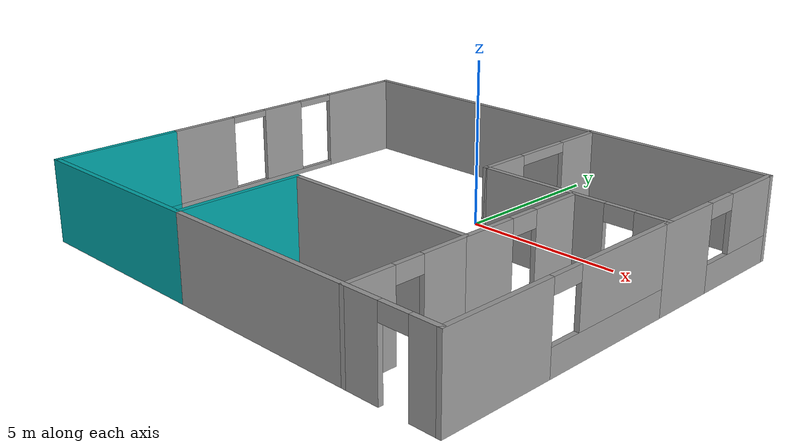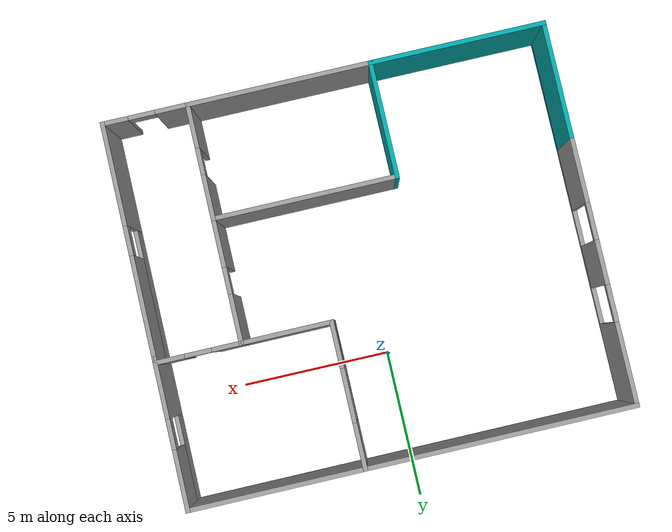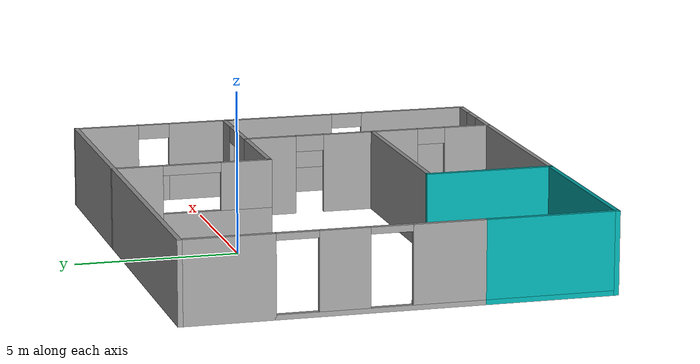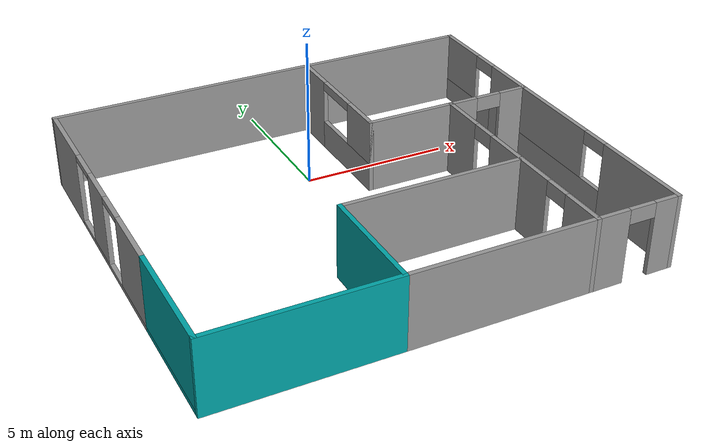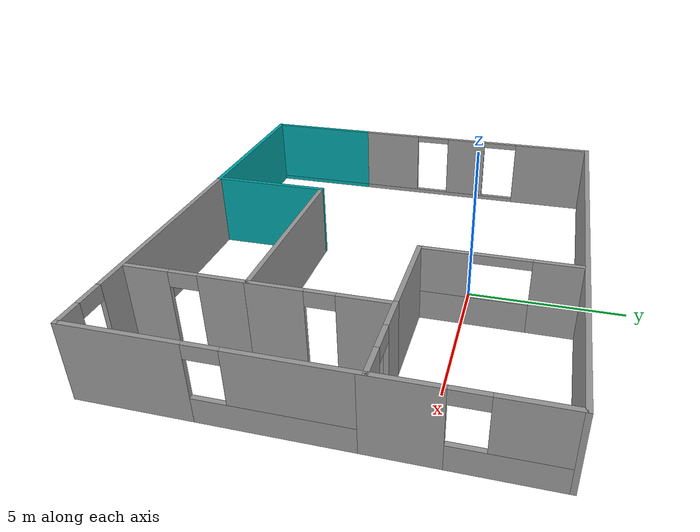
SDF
<?xml version='1.0'?>
<sdf version='1.7'>
  <model name='my_building_p4'>
    <link name='Wall_27'>
      <pose>0 3.46508 0 0 -0 3.14159</pose>
      <self_collide>0</self_collide>
      <enable_wind>0</enable_wind>
      <kinematic>0</kinematic>
      <visual name='Wall_27_Visual'>
        <pose>0 0 1.25 0 -0 0</pose>
        <geometry>
          <box>
            <size>15 0.15 2.5</size>
          </box>
        </geometry>
        <material>
          <script>
            <uri>file://media/materials/scripts/gazebo.material</uri>
            <name>Gazebo/Grey</name>
          </script>
          <ambient>1 1 1 1</ambient>
          <shader type='pixel'/>
        </material>
        <meta>
          <layer>0</layer>
        </meta>
        <transparency>0</transparency>
        <cast_shadows>1</cast_shadows>
      </visual>
      <collision name='Wall_27_Collision'>
        <laser_retro>0</laser_retro>
        <max_contacts>10</max_contacts>
        <pose>0 0 1.25 0 -0 0</pose>
        <geometry>
          <box>
            <size>15 0.15 2.5</size>
          </box>
        </geometry>
        <surface>
          <friction>
            <ode>
              <mu>1</mu>
              <mu2>1</mu2>
              <fdir1>0 0 0</fdir1>
              <slip1>0</slip1>
              <slip2>0</slip2>
            </ode>
            <torsional>
              <coefficient>1</coefficient>
              <patch_radius>0</patch_radius>
              <surface_radius>0</surface_radius>
              <use_patch_radius>1</use_patch_radius>
              <ode>
                <slip>0</slip>
              </ode>
            </torsional>
          </friction>
          <bounce>
            <restitution_coefficient>0</restitution_coefficient>
            <threshold>1e+06</threshold>
          </bounce>
          <contact>
            <collide_without_contact>0</collide_without_contact>
            <collide_without_contact_bitmask>1</collide_without_contact_bitmask>
            <collide_bitmask>1</collide_bitmask>
            <ode>
              <soft_cfm>0</soft_cfm>
              <soft_erp>0.2</soft_erp>
              <kp>1e+13</kp>
              <kd>1</kd>
              <max_vel>0.01</max_vel>
              <min_depth>0</min_depth>
            </ode>
            <bullet>
              <split_impulse>1</split_impulse>
              <split_impulse_penetration_threshold>-0.01</split_impulse_penetration_threshold>
              <soft_cfm>0</soft_cfm>
              <soft_erp>0.2</soft_erp>
              <kp>1e+13</kp>
              <kd>1</kd>
            </bullet>
          </contact>
        </surface>
      </collision>
    </link>
    <link name='Wall_28'>
      <pose>-7.42497 -2.95624 0 0 0 -1.5708</pose>
      <self_collide>0</self_collide>
      <enable_wind>0</enable_wind>
      <kinematic>0</kinematic>
      <gravity>1</gravity>
      <inertial>
        <mass>1</mass>
        <pose>0 0 0 0 -0 0</pose>
        <inertia>
          <ixx>1</ixx>
          <ixy>0</ixy>
          <ixz>0</ixz>
          <iyy>1</iyy>
          <iyz>0</iyz>
          <izz>1</izz>
        </inertia>
      </inertial>
      <visual name='Wall_28_Visual_3'>
        <pose>4.5 0 1.325 0 -0 0</pose>
        <geometry>
          <box>
            <size>4 0.15 2.35</size>
          </box>
        </geometry>
        <material>
          <script>
            <uri>file://media/materials/scripts/gazebo.material</uri>
            <name>Gazebo/Grey</name>
          </script>
          <ambient>0 0.647 0.655 1</ambient>
          <shader type='pixel'>
            <normal_map>__default__</normal_map>
          </shader>
          <diffuse>0 0.647 0.655 1</diffuse>
          <specular>0.01 0.01 0.01 1</specular>
          <emissive>0 0 0 1</emissive>
        </material>
        <meta>
          <layer>0</layer>
        </meta>
        <transparency>0</transparency>
        <cast_shadows>1</cast_shadows>
      </visual>
      <visual name='Wall_28_Visual_2'>
        <pose>4.5 0 0.075 0 -0 0</pose>
        <geometry>
          <box>
            <size>4 0.15 0.15</size>
          </box>
        </geometry>
        <material>
          <script>
            <uri>file://media/materials/scripts/gazebo.material</uri>
            <name>Gazebo/Grey</name>
          </script>
          <ambient>0 0.647 0.655 1</ambient>
          <shader type='pixel'>
            <normal_map>__default__</normal_map>
          </shader>
          <diffuse>0 0.647 0.655 1</diffuse>
          <specular>0.01 0.01 0.01 1</specular>
          <emissive>0 0 0 1</emissive>
        </material>
        <meta>
          <layer>0</layer>
        </meta>
        <transparency>0</transparency>
        <cast_shadows>1</cast_shadows>
      </visual>
      <visual name='Wall_28_Visual_1'>
        <pose>-0.6 0 0.075 0 -0 0</pose>
        <geometry>
          <box>
            <size>6.2 0.15 0.15</size>
          </box>
        </geometry>
        <material>
          <script>
            <uri>file://media/materials/scripts/gazebo.material</uri>
            <name>Gazebo/Grey</name>
          </script>
          <ambient>1 1 1 1</ambient>
          <shader type='pixel'>
            <normal_map>__default__</normal_map>
          </shader>
          <diffuse>0.7 0.7 0.7 1</diffuse>
          <specular>0.01 0.01 0.01 1</specular>
          <emissive>0 0 0 1</emissive>
        </material>
        <meta>
          <layer>0</layer>
        </meta>
        <transparency>0</transparency>
        <cast_shadows>1</cast_shadows>
      </visual>
      <visual name='Wall_28_Visual_5'>
        <pose>-1.663 0 1.325 0 -0 0</pose>
        <geometry>
          <box>
            <size>1.5 0.15 2.35</size>
          </box>
        </geometry>
        <material>
          <script>
            <uri>file://media/materials/scripts/gazebo.material</uri>
            <name>Gazebo/Grey</name>
          </script>
          <ambient>1 1 1 1</ambient>
          <shader type='pixel'>
            <normal_map>__default__</normal_map>
          </shader>
          <diffuse>0.7 0.7 0.7 1</diffuse>
          <specular>0.01 0.01 0.01 1</specular>
          <emissive>0 0 0 1</emissive>
        </material>
        <meta>
          <layer>0</layer>
        </meta>
        <transparency>0</transparency>
        <cast_shadows>1</cast_shadows>
      </visual>
      <visual name='Wall_28_Visual_8'>
        <pose>-3.038 0 2.4 0 -0 0</pose>
        <geometry>
          <box>
            <size>1.25 0.15 0.2</size>
          </box>
        </geometry>
        <material>
          <script>
            <uri>file://media/materials/scripts/gazebo.material</uri>
            <name>Gazebo/Grey</name>
          </script>
          <ambient>1 1 1 1</ambient>
          <shader type='pixel'>
            <normal_map>__default__</normal_map>
          </shader>
          <diffuse>0.7 0.7 0.7 1</diffuse>
          <specular>0.01 0.01 0.01 1</specular>
          <emissive>0 0 0 1</emissive>
        </material>
        <meta>
          <layer>0</layer>
        </meta>
        <transparency>0</transparency>
        <cast_shadows>1</cast_shadows>
      </visual>
      <visual name='Wall_28_Visual_0'>
        <pose>-5.012 0 1.25 0 -0 0</pose>
        <geometry>
          <box>
            <size>2.7 0.15 2.5</size>
          </box>
        </geometry>
        <material>
          <script>
            <uri>file://media/materials/scripts/gazebo.material</uri>
            <name>Gazebo/Grey</name>
          </script>
          <ambient>1 1 1 1</ambient>
          <shader type='pixel'>
            <normal_map>__default__</normal_map>
          </shader>
          <diffuse>0.7 0.7 0.7 1</diffuse>
          <specular>0.01 0.01 0.01 1</specular>
          <emissive>0 0 0 1</emissive>
        </material>
        <meta>
          <layer>0</layer>
        </meta>
        <transparency>0</transparency>
        <cast_shadows>1</cast_shadows>
      </visual>
      <visual name='Wall_28_Visual_6'>
        <pose>-0.288 0 2.4 0 -0 0</pose>
        <geometry>
          <box>
            <size>1.25 0.15 0.2</size>
          </box>
        </geometry>
        <material>
          <script>
            <uri>file://media/materials/scripts/gazebo.material</uri>
            <name>Gazebo/Grey</name>
          </script>
          <ambient>1 1 1 1</ambient>
          <shader type='pixel'>
            <normal_map>__default__</normal_map>
          </shader>
          <diffuse>0.7 0.7 0.7 1</diffuse>
          <specular>0.01 0.01 0.01 1</specular>
          <emissive>0 0 0 1</emissive>
        </material>
        <meta>
          <layer>0</layer>
        </meta>
        <transparency>0</transparency>
        <cast_shadows>1</cast_shadows>
      </visual>
      <collision name='Wall_28_Collision_5'>
        <laser_retro>0</laser_retro>
        <max_contacts>10</max_contacts>
        <pose>-1.663 0 1.325 0 -0 0</pose>
        <geometry>
          <box>
            <size>1.5 0.15 2.35</size>
          </box>
        </geometry>
        <surface>
          <friction>
            <ode>
              <mu>1</mu>
              <mu2>1</mu2>
              <fdir1>0 0 0</fdir1>
              <slip1>0</slip1>
              <slip2>0</slip2>
            </ode>
            <torsional>
              <coefficient>1</coefficient>
              <patch_radius>0</patch_radius>
              <surface_radius>0</surface_radius>
              <use_patch_radius>1</use_patch_radius>
              <ode>
                <slip>0</slip>
              </ode>
            </torsional>
          </friction>
          <bounce>
            <restitution_coefficient>0</restitution_coefficient>
            <threshold>1e+06</threshold>
          </bounce>
          <contact>
            <collide_without_contact>0</collide_without_contact>
            <collide_without_contact_bitmask>1</collide_without_contact_bitmask>
            <collide_bitmask>1</collide_bitmask>
            <ode>
              <soft_cfm>0</soft_cfm>
              <soft_erp>0.2</soft_erp>
              <kp>1e+13</kp>
              <kd>1</kd>
              <max_vel>0.01</max_vel>
              <min_depth>0</min_depth>
            </ode>
            <bullet>
              <split_impulse>1</split_impulse>
              <split_impulse_penetration_threshold>-0.01</split_impulse_penetration_threshold>
              <soft_cfm>0</soft_cfm>
              <soft_erp>0.2</soft_erp>
              <kp>1e+13</kp>
              <kd>1</kd>
            </bullet>
          </contact>
        </surface>
      </collision>
      <collision name='Wall_28_Collision_6'>
        <laser_retro>0</laser_retro>
        <max_contacts>10</max_contacts>
        <pose>-0.288 0 2.4 0 -0 0</pose>
        <geometry>
          <box>
            <size>1.25 0.15 0.2</size>
          </box>
        </geometry>
        <surface>
          <friction>
            <ode>
              <mu>1</mu>
              <mu2>1</mu2>
              <fdir1>0 0 0</fdir1>
              <slip1>0</slip1>
              <slip2>0</slip2>
            </ode>
            <torsional>
              <coefficient>1</coefficient>
              <patch_radius>0</patch_radius>
              <surface_radius>0</surface_radius>
              <use_patch_radius>1</use_patch_radius>
              <ode>
                <slip>0</slip>
              </ode>
            </torsional>
          </friction>
          <bounce>
            <restitution_coefficient>0</restitution_coefficient>
            <threshold>1e+06</threshold>
          </bounce>
          <contact>
            <collide_without_contact>0</collide_without_contact>
            <collide_without_contact_bitmask>1</collide_without_contact_bitmask>
            <collide_bitmask>1</collide_bitmask>
            <ode>
              <soft_cfm>0</soft_cfm>
              <soft_erp>0.2</soft_erp>
              <kp>1e+13</kp>
              <kd>1</kd>
              <max_vel>0.01</max_vel>
              <min_depth>0</min_depth>
            </ode>
            <bullet>
              <split_impulse>1</split_impulse>
              <split_impulse_penetration_threshold>-0.01</split_impulse_penetration_threshold>
              <soft_cfm>0</soft_cfm>
              <soft_erp>0.2</soft_erp>
              <kp>1e+13</kp>
              <kd>1</kd>
            </bullet>
          </contact>
        </surface>
      </collision>
      <collision name='Wall_28_Collision_8'>
        <laser_retro>0</laser_retro>
        <max_contacts>10</max_contacts>
        <pose>-3.038 0 2.4 0 -0 0</pose>
        <geometry>
          <box>
            <size>1.25 0.15 0.2</size>
          </box>
        </geometry>
        <surface>
          <friction>
            <ode>
              <mu>1</mu>
              <mu2>1</mu2>
              <fdir1>0 0 0</fdir1>
              <slip1>0</slip1>
              <slip2>0</slip2>
            </ode>
            <torsional>
              <coefficient>1</coefficient>
              <patch_radius>0</patch_radius>
              <surface_radius>0</surface_radius>
              <use_patch_radius>1</use_patch_radius>
              <ode>
                <slip>0</slip>
              </ode>
            </torsional>
          </friction>
          <bounce>
            <restitution_coefficient>0</restitution_coefficient>
            <threshold>1e+06</threshold>
          </bounce>
          <contact>
            <collide_without_contact>0</collide_without_contact>
            <collide_without_contact_bitmask>1</collide_without_contact_bitmask>
            <collide_bitmask>1</collide_bitmask>
            <ode>
              <soft_cfm>0</soft_cfm>
              <soft_erp>0.2</soft_erp>
              <kp>1e+13</kp>
              <kd>1</kd>
              <max_vel>0.01</max_vel>
              <min_depth>0</min_depth>
            </ode>
            <bullet>
              <split_impulse>1</split_impulse>
              <split_impulse_penetration_threshold>-0.01</split_impulse_penetration_threshold>
              <soft_cfm>0</soft_cfm>
              <soft_erp>0.2</soft_erp>
              <kp>1e+13</kp>
              <kd>1</kd>
            </bullet>
          </contact>
        </surface>
      </collision>
      <collision name='Wall_28_Collision_0'>
        <laser_retro>0</laser_retro>
        <max_contacts>10</max_contacts>
        <pose>-5.012 0 1.25 0 -0 0</pose>
        <geometry>
          <box>
            <size>2.7 0.15 2.5</size>
          </box>
        </geometry>
        <surface>
          <friction>
            <ode>
              <mu>1</mu>
              <mu2>1</mu2>
              <fdir1>0 0 0</fdir1>
              <slip1>0</slip1>
              <slip2>0</slip2>
            </ode>
            <torsional>
              <coefficient>1</coefficient>
              <patch_radius>0</patch_radius>
              <surface_radius>0</surface_radius>
              <use_patch_radius>1</use_patch_radius>
              <ode>
                <slip>0</slip>
              </ode>
            </torsional>
          </friction>
          <bounce>
            <restitution_coefficient>0</restitution_coefficient>
            <threshold>1e+06</threshold>
          </bounce>
          <contact>
            <collide_without_contact>0</collide_without_contact>
            <collide_without_contact_bitmask>1</collide_without_contact_bitmask>
            <collide_bitmask>1</collide_bitmask>
            <ode>
              <soft_cfm>0</soft_cfm>
              <soft_erp>0.2</soft_erp>
              <kp>1e+13</kp>
              <kd>1</kd>
              <max_vel>0.01</max_vel>
              <min_depth>0</min_depth>
            </ode>
            <bullet>
              <split_impulse>1</split_impulse>
              <split_impulse_penetration_threshold>-0.01</split_impulse_penetration_threshold>
              <soft_cfm>0</soft_cfm>
              <soft_erp>0.2</soft_erp>
              <kp>1e+13</kp>
              <kd>1</kd>
            </bullet>
          </contact>
        </surface>
      </collision>
      <collision name='Wall_28_Collision_1'>
        <laser_retro>0</laser_retro>
        <max_contacts>10</max_contacts>
        <pose>-0.6 0 0.075 0 -0 0</pose>
        <geometry>
          <box>
            <size>6.2 0.15 0.15</size>
          </box>
        </geometry>
        <surface>
          <friction>
            <ode>
              <mu>1</mu>
              <mu2>1</mu2>
              <fdir1>0 0 0</fdir1>
              <slip1>0</slip1>
              <slip2>0</slip2>
            </ode>
            <torsional>
              <coefficient>1</coefficient>
              <patch_radius>0</patch_radius>
              <surface_radius>0</surface_radius>
              <use_patch_radius>1</use_patch_radius>
              <ode>
                <slip>0</slip>
              </ode>
            </torsional>
          </friction>
          <bounce>
            <restitution_coefficient>0</restitution_coefficient>
            <threshold>1e+06</threshold>
          </bounce>
          <contact>
            <collide_without_contact>0</collide_without_contact>
            <collide_without_contact_bitmask>1</collide_without_contact_bitmask>
            <collide_bitmask>1</collide_bitmask>
            <ode>
              <soft_cfm>0</soft_cfm>
              <soft_erp>0.2</soft_erp>
              <kp>1e+13</kp>
              <kd>1</kd>
              <max_vel>0.01</max_vel>
              <min_depth>0</min_depth>
            </ode>
            <bullet>
              <split_impulse>1</split_impulse>
              <split_impulse_penetration_threshold>-0.01</split_impulse_penetration_threshold>
              <soft_cfm>0</soft_cfm>
              <soft_erp>0.2</soft_erp>
              <kp>1e+13</kp>
              <kd>1</kd>
            </bullet>
          </contact>
        </surface>
      </collision>
      <collision name='Wall_28_Collision_3'>
        <laser_retro>0</laser_retro>
        <max_contacts>10</max_contacts>
        <pose>4.5 0 1.325 0 -0 0</pose>
        <geometry>
          <box>
            <size>4 0.15 2.35</size>
          </box>
        </geometry>
        <surface>
          <friction>
            <ode>
              <mu>1</mu>
              <mu2>1</mu2>
              <fdir1>0 0 0</fdir1>
              <slip1>0</slip1>
              <slip2>0</slip2>
            </ode>
            <torsional>
              <coefficient>1</coefficient>
              <patch_radius>0</patch_radius>
              <surface_radius>0</surface_radius>
              <use_patch_radius>1</use_patch_radius>
              <ode>
                <slip>0</slip>
              </ode>
            </torsional>
          </friction>
          <bounce>
            <restitution_coefficient>0</restitution_coefficient>
            <threshold>1e+06</threshold>
          </bounce>
          <contact>
            <collide_without_contact>0</collide_without_contact>
            <collide_without_contact_bitmask>1</collide_without_contact_bitmask>
            <collide_bitmask>1</collide_bitmask>
            <ode>
              <soft_cfm>0</soft_cfm>
              <soft_erp>0.2</soft_erp>
              <kp>1e+13</kp>
              <kd>1</kd>
              <max_vel>0.01</max_vel>
              <min_depth>0</min_depth>
            </ode>
            <bullet>
              <split_impulse>1</split_impulse>
              <split_impulse_penetration_threshold>-0.01</split_impulse_penetration_threshold>
              <soft_cfm>0</soft_cfm>
              <soft_erp>0.2</soft_erp>
              <kp>1e+13</kp>
              <kd>1</kd>
            </bullet>
          </contact>
        </surface>
      </collision>
      <collision name='Wall_28_Collision_2'>
        <laser_retro>0</laser_retro>
        <max_contacts>10</max_contacts>
        <pose>4.5 0 0.075 0 -0 0</pose>
        <geometry>
          <box>
            <size>4 0.15 0.15</size>
          </box>
        </geometry>
        <surface>
          <friction>
            <ode>
              <mu>1</mu>
              <mu2>1</mu2>
              <fdir1>0 0 0</fdir1>
              <slip1>0</slip1>
              <slip2>0</slip2>
            </ode>
            <torsional>
              <coefficient>1</coefficient>
              <patch_radius>0</patch_radius>
              <surface_radius>0</surface_radius>
              <use_patch_radius>1</use_patch_radius>
              <ode>
                <slip>0</slip>
              </ode>
            </torsional>
          </friction>
          <bounce>
            <restitution_coefficient>0</restitution_coefficient>
            <threshold>1e+06</threshold>
          </bounce>
          <contact>
            <collide_without_contact>0</collide_without_contact>
            <collide_without_contact_bitmask>1</collide_without_contact_bitmask>
            <collide_bitmask>1</collide_bitmask>
            <ode>
              <soft_cfm>0</soft_cfm>
              <soft_erp>0.2</soft_erp>
              <kp>1e+13</kp>
              <kd>1</kd>
              <max_vel>0.01</max_vel>
              <min_depth>0</min_depth>
            </ode>
            <bullet>
              <split_impulse>1</split_impulse>
              <split_impulse_penetration_threshold>-0.01</split_impulse_penetration_threshold>
              <soft_cfm>0</soft_cfm>
              <soft_erp>0.2</soft_erp>
              <kp>1e+13</kp>
              <kd>1</kd>
            </bullet>
          </contact>
        </surface>
      </collision>
    </link>
    <link name='Wall_28_clone'>
      <pose>-7.42533 -5.43108 0 0 0 -1.5708</pose>
      <self_collide>0</self_collide>
      <enable_wind>0</enable_wind>
      <kinematic>0</kinematic>
      <gravity>1</gravity>
      <inertial>
        <mass>1</mass>
        <pose>0 0 0 0 -0 0</pose>
        <inertia>
          <ixx>1</ixx>
          <ixy>0</ixy>
          <ixz>0</ixz>
          <iyy>1</iyy>
          <iyz>0</iyz>
          <izz>1</izz>
        </inertia>
      </inertial>
      <visual name='Wall_28_Visual_5'>
        <pose>-1.058 0 1.325 0 -0 0</pose>
        <geometry>
          <box>
            <size>2.16667 0.15 2.35</size>
          </box>
        </geometry>
        <material>
          <script>
            <uri>file://media/materials/scripts/gazebo.material</uri>
            <name>Gazebo/Grey</name>
          </script>
          <ambient>1 1 1 1</ambient>
          <shader type='pixel'>
            <normal_map>__default__</normal_map>
          </shader>
          <diffuse>0.7 0.7 0.7 1</diffuse>
          <specular>0.01 0.01 0.01 1</specular>
          <emissive>0 0 0 1</emissive>
        </material>
        <meta>
          <layer>0</layer>
        </meta>
        <transparency>0</transparency>
        <cast_shadows>1</cast_shadows>
      </visual>
      <collision name='Wall_28_Collision_5'>
        <laser_retro>0</laser_retro>
        <max_contacts>10</max_contacts>
        <pose>-1.058 0 1.325 0 -0 0</pose>
        <geometry>
          <box>
            <size>2.16667 0.15 2.35</size>
          </box>
        </geometry>
        <surface>
          <friction>
            <ode>
              <mu>1</mu>
              <mu2>1</mu2>
              <fdir1>0 0 0</fdir1>
              <slip1>0</slip1>
              <slip2>0</slip2>
            </ode>
            <torsional>
              <coefficient>1</coefficient>
              <patch_radius>0</patch_radius>
              <surface_radius>0</surface_radius>
              <use_patch_radius>1</use_patch_radius>
              <ode>
                <slip>0</slip>
              </ode>
            </torsional>
          </friction>
          <bounce>
            <restitution_coefficient>0</restitution_coefficient>
            <threshold>1e+06</threshold>
          </bounce>
          <contact>
            <collide_without_contact>0</collide_without_contact>
            <collide_without_contact_bitmask>1</collide_without_contact_bitmask>
            <collide_bitmask>1</collide_bitmask>
            <ode>
              <soft_cfm>0</soft_cfm>
              <soft_erp>0.2</soft_erp>
              <kp>1e+13</kp>
              <kd>1</kd>
              <max_vel>0.01</max_vel>
              <min_depth>0</min_depth>
            </ode>
            <bullet>
              <split_impulse>1</split_impulse>
              <split_impulse_penetration_threshold>-0.01</split_impulse_penetration_threshold>
              <soft_cfm>0</soft_cfm>
              <soft_erp>0.2</soft_erp>
              <kp>1e+13</kp>
              <kd>1</kd>
            </bullet>
          </contact>
        </surface>
      </collision>
    </link>
    <link name='Wall_29'>
      <pose>-4.5 -9.38492 0 0 -0 0</pose>
      <self_collide>0</self_collide>
      <enable_wind>0</enable_wind>
      <kinematic>0</kinematic>
      <gravity>1</gravity>
      <inertial>
        <mass>1</mass>
        <pose>0 0 0 0 -0 0</pose>
        <inertia>
          <ixx>1</ixx>
          <ixy>0</ixy>
          <ixz>0</ixz>
          <iyy>1</iyy>
          <iyz>0</iyz>
          <izz>1</izz>
        </inertia>
      </inertial>
      <visual name='Wall_29_Visual'>
        <pose>0 0 1.25 0 -0 0</pose>
        <geometry>
          <box>
            <size>6 0.15 2.5</size>
          </box>
        </geometry>
        <material>
          <script>
            <uri>file://media/materials/scripts/gazebo.material</uri>
            <name>Gazebo/Grey</name>
          </script>
          <ambient>0 0.647 0.655 1</ambient>
          <shader type='pixel'>
            <normal_map>__default__</normal_map>
          </shader>
          <diffuse>0 0.647 0.655 1</diffuse>
          <specular>0.01 0.01 0.01 1</specular>
          <emissive>0 0 0 1</emissive>
        </material>
        <meta>
          <layer>0</layer>
        </meta>
        <transparency>0</transparency>
        <cast_shadows>1</cast_shadows>
      </visual>
      <collision name='Wall_29_Collision'>
        <laser_retro>0</laser_retro>
        <max_contacts>10</max_contacts>
        <pose>0 0 1.25 0 -0 0</pose>
        <geometry>
          <box>
            <size>6 0.15 2.5</size>
          </box>
        </geometry>
        <surface>
          <friction>
            <ode>
              <mu>1</mu>
              <mu2>1</mu2>
              <fdir1>0 0 0</fdir1>
              <slip1>0</slip1>
              <slip2>0</slip2>
            </ode>
            <torsional>
              <coefficient>1</coefficient>
              <patch_radius>0</patch_radius>
              <surface_radius>0</surface_radius>
              <use_patch_radius>1</use_patch_radius>
              <ode>
                <slip>0</slip>
              </ode>
            </torsional>
          </friction>
          <bounce>
            <restitution_coefficient>0</restitution_coefficient>
            <threshold>1e+06</threshold>
          </bounce>
          <contact>
            <collide_without_contact>0</collide_without_contact>
            <collide_without_contact_bitmask>1</collide_without_contact_bitmask>
            <collide_bitmask>1</collide_bitmask>
            <ode>
              <soft_cfm>0</soft_cfm>
              <soft_erp>0.2</soft_erp>
              <kp>1e+13</kp>
              <kd>1</kd>
              <max_vel>0.01</max_vel>
              <min_depth>0</min_depth>
            </ode>
            <bullet>
              <split_impulse>1</split_impulse>
              <split_impulse_penetration_threshold>-0.01</split_impulse_penetration_threshold>
              <soft_cfm>0</soft_cfm>
              <soft_erp>0.2</soft_erp>
              <kp>1e+13</kp>
              <kd>1</kd>
            </bullet>
          </contact>
        </surface>
      </collision>
    </link>
    <link name='Wall_30'>
      <pose>-1.57502 -7.45997 0 0 -0 1.57081</pose>
      <self_collide>0</self_collide>
      <enable_wind>0</enable_wind>
      <kinematic>0</kinematic>
      <gravity>1</gravity>
      <inertial>
        <mass>1</mass>
        <pose>0 0 0 0 -0 0</pose>
        <inertia>
          <ixx>1</ixx>
          <ixy>0</ixy>
          <ixz>0</ixz>
          <iyy>1</iyy>
          <iyz>0</iyz>
          <izz>1</izz>
        </inertia>
      </inertial>
      <visual name='Wall_30_Visual'>
        <pose>0 0 1.25 0 -0 0</pose>
        <geometry>
          <box>
            <size>3.99989 0.15 2.5</size>
          </box>
        </geometry>
        <material>
          <script>
            <uri>file://media/materials/scripts/gazebo.material</uri>
            <name>Gazebo/Grey</name>
          </script>
          <ambient>0 0.647 0.655 1</ambient>
          <shader type='pixel'>
            <normal_map>__default__</normal_map>
          </shader>
          <diffuse>0 0.647 0.655 1</diffuse>
          <specular>0.01 0.01 0.01 1</specular>
          <emissive>0 0 0 1</emissive>
        </material>
        <meta>
          <layer>0</layer>
        </meta>
        <transparency>0</transparency>
        <cast_shadows>1</cast_shadows>
      </visual>
      <collision name='Wall_30_Collision'>
        <laser_retro>0</laser_retro>
        <max_contacts>10</max_contacts>
        <pose>0 0 1.25 0 -0 0</pose>
        <geometry>
          <box>
            <size>3.99989 0.15 2.5</size>
          </box>
        </geometry>
        <surface>
          <friction>
            <ode>
              <mu>1</mu>
              <mu2>1</mu2>
              <fdir1>0 0 0</fdir1>
              <slip1>0</slip1>
              <slip2>0</slip2>
            </ode>
            <torsional>
              <coefficient>1</coefficient>
              <patch_radius>0</patch_radius>
              <surface_radius>0</surface_radius>
              <use_patch_radius>1</use_patch_radius>
              <ode>
                <slip>0</slip>
              </ode>
            </torsional>
          </friction>
          <bounce>
            <restitution_coefficient>0</restitution_coefficient>
            <threshold>1e+06</threshold>
          </bounce>
          <contact>
            <collide_without_contact>0</collide_without_contact>
            <collide_without_contact_bitmask>1</collide_without_contact_bitmask>
            <collide_bitmask>1</collide_bitmask>
            <ode>
              <soft_cfm>0</soft_cfm>
              <soft_erp>0.2</soft_erp>
              <kp>1e+13</kp>
              <kd>1</kd>
              <max_vel>0.01</max_vel>
              <min_depth>0</min_depth>
            </ode>
            <bullet>
              <split_impulse>1</split_impulse>
              <split_impulse_penetration_threshold>-0.01</split_impulse_penetration_threshold>
              <soft_cfm>0</soft_cfm>
              <soft_erp>0.2</soft_erp>
              <kp>1e+13</kp>
              <kd>1</kd>
            </bullet>
          </contact>
        </surface>
      </collision>
    </link>
    <link name='Wall_32'>
      <pose>2.925 -9.38492 0 0 -0 0</pose>
      <self_collide>0</self_collide>
      <enable_wind>0</enable_wind>
      <kinematic>0</kinematic>
      <gravity>1</gravity>
      <inertial>
        <mass>1</mass>
        <pose>0 0 0 0 -0 0</pose>
        <inertia>
          <ixx>1</ixx>
          <ixy>0</ixy>
          <ixz>0</ixz>
          <iyy>1</iyy>
          <iyz>0</iyz>
          <izz>1</izz>
        </inertia>
      </inertial>
      <visual name='Wall_32_Visual_1'>
        <pose>4.11059 0 1.25 0 -0 0</pose>
        <geometry>
          <box>
            <size>0.928826 0.15 2.5</size>
          </box>
        </geometry>
        <material>
          <script>
            <uri>file://media/materials/scripts/gazebo.material</uri>
            <name>Gazebo/Grey</name>
          </script>
          <ambient>1 1 1 1</ambient>
          <shader type='pixel'>
            <normal_map>__default__</normal_map>
          </shader>
          <diffuse>0.7 0.7 0.7 1</diffuse>
          <specular>0.01 0.01 0.01 1</specular>
          <emissive>0 0 0 1</emissive>
        </material>
        <meta>
          <layer>0</layer>
        </meta>
        <transparency>0</transparency>
        <cast_shadows>1</cast_shadows>
      </visual>
      <visual name='Wall_32_Visual_2'>
        <pose>3.19617 0 2.25 0 -0 0</pose>
        <geometry>
          <box>
            <size>0.9 0.15 0.5</size>
          </box>
        </geometry>
        <material>
          <script>
            <uri>file://media/materials/scripts/gazebo.material</uri>
            <name>Gazebo/Grey</name>
          </script>
          <ambient>1 1 1 1</ambient>
          <shader type='pixel'>
            <normal_map>__default__</normal_map>
          </shader>
          <diffuse>0.7 0.7 0.7 1</diffuse>
          <specular>0.01 0.01 0.01 1</specular>
          <emissive>0 0 0 1</emissive>
        </material>
        <meta>
          <layer>0</layer>
        </meta>
        <transparency>0</transparency>
        <cast_shadows>1</cast_shadows>
      </visual>
      <visual name='Wall_32_Visual_0'>
        <pose>-0.84 0 1.25 0 -0 0</pose>
        <geometry>
          <box>
            <size>7.17 0.15 2.5</size>
          </box>
        </geometry>
        <material>
          <script>
            <uri>file://media/materials/scripts/gazebo.material</uri>
            <name>Gazebo/Grey</name>
          </script>
          <ambient>1 1 1 1</ambient>
          <shader type='pixel'>
            <normal_map>__default__</normal_map>
          </shader>
          <diffuse>0.7 0.7 0.7 1</diffuse>
          <specular>0.01 0.01 0.01 1</specular>
          <emissive>0 0 0 1</emissive>
        </material>
        <meta>
          <layer>0</layer>
        </meta>
        <transparency>0</transparency>
        <cast_shadows>1</cast_shadows>
      </visual>
      <collision name='Wall_32_Collision_1'>
        <laser_retro>0</laser_retro>
        <max_contacts>10</max_contacts>
        <pose>4.11059 0 1.25 0 -0 0</pose>
        <geometry>
          <box>
            <size>0.928826 0.15 2.5</size>
          </box>
        </geometry>
        <surface>
          <friction>
            <ode>
              <mu>1</mu>
              <mu2>1</mu2>
              <fdir1>0 0 0</fdir1>
              <slip1>0</slip1>
              <slip2>0</slip2>
            </ode>
            <torsional>
              <coefficient>1</coefficient>
              <patch_radius>0</patch_radius>
              <surface_radius>0</surface_radius>
              <use_patch_radius>1</use_patch_radius>
              <ode>
                <slip>0</slip>
              </ode>
            </torsional>
          </friction>
          <bounce>
            <restitution_coefficient>0</restitution_coefficient>
            <threshold>1e+06</threshold>
          </bounce>
          <contact>
            <collide_without_contact>0</collide_without_contact>
            <collide_without_contact_bitmask>1</collide_without_contact_bitmask>
            <collide_bitmask>1</collide_bitmask>
            <ode>
              <soft_cfm>0</soft_cfm>
              <soft_erp>0.2</soft_erp>
              <kp>1e+13</kp>
              <kd>1</kd>
              <max_vel>0.01</max_vel>
              <min_depth>0</min_depth>
            </ode>
            <bullet>
              <split_impulse>1</split_impulse>
              <split_impulse_penetration_threshold>-0.01</split_impulse_penetration_threshold>
              <soft_cfm>0</soft_cfm>
              <soft_erp>0.2</soft_erp>
              <kp>1e+13</kp>
              <kd>1</kd>
            </bullet>
          </contact>
        </surface>
      </collision>
      <collision name='Wall_32_Collision_0'>
        <laser_retro>0</laser_retro>
        <max_contacts>10</max_contacts>
        <pose>-0.84 0 1.25 0 -0 0</pose>
        <geometry>
          <box>
            <size>7.17 0.15 2.5</size>
          </box>
        </geometry>
        <surface>
          <friction>
            <ode>
              <mu>1</mu>
              <mu2>1</mu2>
              <fdir1>0 0 0</fdir1>
              <slip1>0</slip1>
              <slip2>0</slip2>
            </ode>
            <torsional>
              <coefficient>1</coefficient>
              <patch_radius>0</patch_radius>
              <surface_radius>0</surface_radius>
              <use_patch_radius>1</use_patch_radius>
              <ode>
                <slip>0</slip>
              </ode>
            </torsional>
          </friction>
          <bounce>
            <restitution_coefficient>0</restitution_coefficient>
            <threshold>1e+06</threshold>
          </bounce>
          <contact>
            <collide_without_contact>0</collide_without_contact>
            <collide_without_contact_bitmask>1</collide_without_contact_bitmask>
            <collide_bitmask>1</collide_bitmask>
            <ode>
              <soft_cfm>0</soft_cfm>
              <soft_erp>0.2</soft_erp>
              <kp>1e+13</kp>
              <kd>1</kd>
              <max_vel>0.01</max_vel>
              <min_depth>0</min_depth>
            </ode>
            <bullet>
              <split_impulse>1</split_impulse>
              <split_impulse_penetration_threshold>-0.01</split_impulse_penetration_threshold>
              <soft_cfm>0</soft_cfm>
              <soft_erp>0.2</soft_erp>
              <kp>1e+13</kp>
              <kd>1</kd>
            </bullet>
          </contact>
        </surface>
      </collision>
      <collision name='Wall_32_Collision_2'>
        <laser_retro>0</laser_retro>
        <max_contacts>10</max_contacts>
        <pose>3.19617 0 2.25 0 -0 0</pose>
        <geometry>
          <box>
            <size>0.9 0.15 0.5</size>
          </box>
        </geometry>
        <surface>
          <friction>
            <ode>
              <mu>1</mu>
              <mu2>1</mu2>
              <fdir1>0 0 0</fdir1>
              <slip1>0</slip1>
              <slip2>0</slip2>
            </ode>
            <torsional>
              <coefficient>1</coefficient>
              <patch_radius>0</patch_radius>
              <surface_radius>0</surface_radius>
              <use_patch_radius>1</use_patch_radius>
              <ode>
                <slip>0</slip>
              </ode>
            </torsional>
          </friction>
          <bounce>
            <restitution_coefficient>0</restitution_coefficient>
            <threshold>1e+06</threshold>
          </bounce>
          <contact>
            <collide_without_contact>0</collide_without_contact>
            <collide_without_contact_bitmask>1</collide_without_contact_bitmask>
            <collide_bitmask>1</collide_bitmask>
            <ode>
              <soft_cfm>0</soft_cfm>
              <soft_erp>0.2</soft_erp>
              <kp>1e+13</kp>
              <kd>1</kd>
              <max_vel>0.01</max_vel>
              <min_depth>0</min_depth>
            </ode>
            <bullet>
              <split_impulse>1</split_impulse>
              <split_impulse_penetration_threshold>-0.01</split_impulse_penetration_threshold>
              <soft_cfm>0</soft_cfm>
              <soft_erp>0.2</soft_erp>
              <kp>1e+13</kp>
              <kd>1</kd>
            </bullet>
          </contact>
        </surface>
      </collision>
    </link>
    <link name='Wall_36'>
      <pose>1.49997 -5.53503 0 0 -0 0</pose>
      <self_collide>0</self_collide>
      <enable_wind>0</enable_wind>
      <kinematic>0</kinematic>
      <gravity>1</gravity>
      <inertial>
        <mass>1</mass>
        <pose>0 0 0 0 -0 0</pose>
        <inertia>
          <ixx>1</ixx>
          <ixy>0</ixy>
          <ixz>0</ixz>
          <iyy>1</iyy>
          <iyz>0</iyz>
          <izz>1</izz>
        </inertia>
      </inertial>
      <visual name='Wall_36_Visual'>
        <pose>0 0 1.25 0 -0 0</pose>
        <geometry>
          <box>
            <size>6 0.15 2.5</size>
          </box>
        </geometry>
        <material>
          <script>
            <uri>file://media/materials/scripts/gazebo.material</uri>
            <name>Gazebo/Grey</name>
          </script>
          <ambient>1 1 1 1</ambient>
          <shader type='pixel'>
            <normal_map>__default__</normal_map>
          </shader>
          <diffuse>0.7 0.7 0.7 1</diffuse>
          <specular>0.01 0.01 0.01 1</specular>
          <emissive>0 0 0 1</emissive>
        </material>
        <meta>
          <layer>0</layer>
        </meta>
        <transparency>0</transparency>
        <cast_shadows>1</cast_shadows>
      </visual>
      <collision name='Wall_36_Collision'>
        <laser_retro>0</laser_retro>
        <max_contacts>10</max_contacts>
        <pose>0 0 1.25 0 -0 0</pose>
        <geometry>
          <box>
            <size>6 0.15 2.5</size>
          </box>
        </geometry>
        <surface>
          <friction>
            <ode>
              <mu>1</mu>
              <mu2>1</mu2>
              <fdir1>0 0 0</fdir1>
              <slip1>0</slip1>
              <slip2>0</slip2>
            </ode>
            <torsional>
              <coefficient>1</coefficient>
              <patch_radius>0</patch_radius>
              <surface_radius>0</surface_radius>
              <use_patch_radius>1</use_patch_radius>
              <ode>
                <slip>0</slip>
              </ode>
            </torsional>
          </friction>
          <bounce>
            <restitution_coefficient>0</restitution_coefficient>
            <threshold>1e+06</threshold>
          </bounce>
          <contact>
            <collide_without_contact>0</collide_without_contact>
            <collide_without_contact_bitmask>1</collide_without_contact_bitmask>
            <collide_bitmask>1</collide_bitmask>
            <ode>
              <soft_cfm>0</soft_cfm>
              <soft_erp>0.2</soft_erp>
              <kp>1e+13</kp>
              <kd>1</kd>
              <max_vel>0.01</max_vel>
              <min_depth>0</min_depth>
            </ode>
            <bullet>
              <split_impulse>1</split_impulse>
              <split_impulse_penetration_threshold>-0.01</split_impulse_penetration_threshold>
              <soft_cfm>0</soft_cfm>
              <soft_erp>0.2</soft_erp>
              <kp>1e+13</kp>
              <kd>1</kd>
            </bullet>
          </contact>
        </surface>
      </collision>
    </link>
    <link name='Wall_37'>
      <pose>4.57498 -7.45997 0 0 0 -1.57079</pose>
      <self_collide>0</self_collide>
      <enable_wind>0</enable_wind>
      <kinematic>0</kinematic>
      <visual name='Wall_37_Visual_0'>
        <pose>-1.22294 0 1.25 0 -0 0</pose>
        <geometry>
          <box>
            <size>1.55413 0.15 2.5</size>
          </box>
        </geometry>
        <material>
          <script>
            <uri>file://media/materials/scripts/gazebo.material</uri>
            <name>Gazebo/Grey</name>
          </script>
          <ambient>1 1 1 1</ambient>
          <shader type='pixel'/>
        </material>
        <meta>
          <layer>0</layer>
        </meta>
        <transparency>0</transparency>
        <cast_shadows>1</cast_shadows>
      </visual>
      <visual name='Wall_37_Visual_2'>
        <pose>0.004129 0 2.25 0 -0 0</pose>
        <geometry>
          <box>
            <size>0.9 0.15 0.5</size>
          </box>
        </geometry>
        <material>
          <script>
            <uri>file://media/materials/scripts/gazebo.material</uri>
            <name>Gazebo/Grey</name>
          </script>
          <ambient>1 1 1 1</ambient>
          <shader type='pixel'/>
        </material>
        <meta>
          <layer>0</layer>
        </meta>
        <transparency>0</transparency>
        <cast_shadows>1</cast_shadows>
      </visual>
      <visual name='Wall_37_Visual_1'>
        <pose>1.22707 0 1.25 0 -0 0</pose>
        <geometry>
          <box>
            <size>1.54587 0.15 2.5</size>
          </box>
        </geometry>
        <material>
          <script>
            <uri>file://media/materials/scripts/gazebo.material</uri>
            <name>Gazebo/Grey</name>
          </script>
          <ambient>1 1 1 1</ambient>
          <shader type='pixel'/>
        </material>
        <meta>
          <layer>0</layer>
        </meta>
        <transparency>0</transparency>
        <cast_shadows>1</cast_shadows>
      </visual>
      <collision name='Wall_37_Collision_0'>
        <laser_retro>0</laser_retro>
        <max_contacts>10</max_contacts>
        <pose>-1.22294 0 1.25 0 -0 0</pose>
        <geometry>
          <box>
            <size>1.55413 0.15 2.5</size>
          </box>
        </geometry>
        <surface>
          <friction>
            <ode>
              <mu>1</mu>
              <mu2>1</mu2>
              <fdir1>0 0 0</fdir1>
              <slip1>0</slip1>
              <slip2>0</slip2>
            </ode>
            <torsional>
              <coefficient>1</coefficient>
              <patch_radius>0</patch_radius>
              <surface_radius>0</surface_radius>
              <use_patch_radius>1</use_patch_radius>
              <ode>
                <slip>0</slip>
              </ode>
            </torsional>
          </friction>
          <bounce>
            <restitution_coefficient>0</restitution_coefficient>
            <threshold>1e+06</threshold>
          </bounce>
          <contact>
            <collide_without_contact>0</collide_without_contact>
            <collide_without_contact_bitmask>1</collide_without_contact_bitmask>
            <collide_bitmask>1</collide_bitmask>
            <ode>
              <soft_cfm>0</soft_cfm>
              <soft_erp>0.2</soft_erp>
              <kp>1e+13</kp>
              <kd>1</kd>
              <max_vel>0.01</max_vel>
              <min_depth>0</min_depth>
            </ode>
            <bullet>
              <split_impulse>1</split_impulse>
              <split_impulse_penetration_threshold>-0.01</split_impulse_penetration_threshold>
              <soft_cfm>0</soft_cfm>
              <soft_erp>0.2</soft_erp>
              <kp>1e+13</kp>
              <kd>1</kd>
            </bullet>
          </contact>
        </surface>
      </collision>
      <collision name='Wall_37_Collision_1'>
        <laser_retro>0</laser_retro>
        <max_contacts>10</max_contacts>
        <pose>1.22707 0 1.25 0 -0 0</pose>
        <geometry>
          <box>
            <size>1.54587 0.15 2.5</size>
          </box>
        </geometry>
        <surface>
          <friction>
            <ode>
              <mu>1</mu>
              <mu2>1</mu2>
              <fdir1>0 0 0</fdir1>
              <slip1>0</slip1>
              <slip2>0</slip2>
            </ode>
            <torsional>
              <coefficient>1</coefficient>
              <patch_radius>0</patch_radius>
              <surface_radius>0</surface_radius>
              <use_patch_radius>1</use_patch_radius>
              <ode>
                <slip>0</slip>
              </ode>
            </torsional>
          </friction>
          <bounce>
            <restitution_coefficient>0</restitution_coefficient>
            <threshold>1e+06</threshold>
          </bounce>
          <contact>
            <collide_without_contact>0</collide_without_contact>
            <collide_without_contact_bitmask>1</collide_without_contact_bitmask>
            <collide_bitmask>1</collide_bitmask>
            <ode>
              <soft_cfm>0</soft_cfm>
              <soft_erp>0.2</soft_erp>
              <kp>1e+13</kp>
              <kd>1</kd>
              <max_vel>0.01</max_vel>
              <min_depth>0</min_depth>
            </ode>
            <bullet>
              <split_impulse>1</split_impulse>
              <split_impulse_penetration_threshold>-0.01</split_impulse_penetration_threshold>
              <soft_cfm>0</soft_cfm>
              <soft_erp>0.2</soft_erp>
              <kp>1e+13</kp>
              <kd>1</kd>
            </bullet>
          </contact>
        </surface>
      </collision>
      <collision name='Wall_37_Collision_2'>
        <laser_retro>0</laser_retro>
        <max_contacts>10</max_contacts>
        <pose>0.004129 0 2.25 0 -0 0</pose>
        <geometry>
          <box>
            <size>0.9 0.15 0.5</size>
          </box>
        </geometry>
        <surface>
          <friction>
            <ode>
              <mu>1</mu>
              <mu2>1</mu2>
              <fdir1>0 0 0</fdir1>
              <slip1>0</slip1>
              <slip2>0</slip2>
            </ode>
            <torsional>
              <coefficient>1</coefficient>
              <patch_radius>0</patch_radius>
              <surface_radius>0</surface_radius>
              <use_patch_radius>1</use_patch_radius>
              <ode>
                <slip>0</slip>
              </ode>
            </torsional>
          </friction>
          <bounce>
            <restitution_coefficient>0</restitution_coefficient>
            <threshold>1e+06</threshold>
          </bounce>
          <contact>
            <collide_without_contact>0</collide_without_contact>
            <collide_without_contact_bitmask>1</collide_without_contact_bitmask>
            <collide_bitmask>1</collide_bitmask>
            <ode>
              <soft_cfm>0</soft_cfm>
              <soft_erp>0.2</soft_erp>
              <kp>1e+13</kp>
              <kd>1</kd>
              <max_vel>0.01</max_vel>
              <min_depth>0</min_depth>
            </ode>
            <bullet>
              <split_impulse>1</split_impulse>
              <split_impulse_penetration_threshold>-0.01</split_impulse_penetration_threshold>
              <soft_cfm>0</soft_cfm>
              <soft_erp>0.2</soft_erp>
              <kp>1e+13</kp>
              <kd>1</kd>
            </bullet>
          </contact>
        </surface>
      </collision>
    </link>
    <link name='Wall_39'>
      <pose>7.425 -5.45992 0 0 -0 1.5708</pose>
      <self_collide>0</self_collide>
      <enable_wind>0</enable_wind>
      <kinematic>0</kinematic>
      <visual name='Wall_39_Visual_3'>
        <pose>0.00913 0 2.275 0 -0 0</pose>
        <geometry>
          <box>
            <size>1 0.15 0.45</size>
          </box>
        </geometry>
        <material>
          <script>
            <uri>file://media/materials/scripts/gazebo.material</uri>
            <name>Gazebo/Grey</name>
          </script>
          <ambient>1 1 1 1</ambient>
          <shader type='pixel'/>
        </material>
        <meta>
          <layer>0</layer>
        </meta>
        <transparency>0</transparency>
        <cast_shadows>1</cast_shadows>
      </visual>
      <visual name='Wall_39_Visual_2'>
        <pose>2.25456 0 1.65 0 -0 0</pose>
        <geometry>
          <box>
            <size>3.49087 0.15 1.7</size>
          </box>
        </geometry>
        <material>
          <script>
            <uri>file://media/materials/scripts/gazebo.material</uri>
            <name>Gazebo/Grey</name>
          </script>
          <ambient>1 1 1 1</ambient>
          <shader type='pixel'/>
        </material>
        <meta>
          <layer>0</layer>
        </meta>
        <transparency>0</transparency>
        <cast_shadows>1</cast_shadows>
      </visual>
      <visual name='Wall_39_Visual_0'>
        <pose>-2.24544 0 1.25 0 -0 0</pose>
        <geometry>
          <box>
            <size>3.50913 0.15 2.5</size>
          </box>
        </geometry>
        <material>
          <script>
            <uri>file://media/materials/scripts/gazebo.material</uri>
            <name>Gazebo/Grey</name>
          </script>
          <ambient>1 1 1 1</ambient>
          <shader type='pixel'/>
        </material>
        <meta>
          <layer>0</layer>
        </meta>
        <transparency>0</transparency>
        <cast_shadows>1</cast_shadows>
      </visual>
      <visual name='Wall_39_Visual_1'>
        <pose>1.75456 0 0.4 0 -0 0</pose>
        <geometry>
          <box>
            <size>4.49087 0.15 0.8</size>
          </box>
        </geometry>
        <material>
          <script>
            <uri>file://media/materials/scripts/gazebo.material</uri>
            <name>Gazebo/Grey</name>
          </script>
          <ambient>1 1 1 1</ambient>
          <shader type='pixel'/>
        </material>
        <meta>
          <layer>0</layer>
        </meta>
        <transparency>0</transparency>
        <cast_shadows>1</cast_shadows>
      </visual>
      <collision name='Wall_39_Collision_1'>
        <laser_retro>0</laser_retro>
        <max_contacts>10</max_contacts>
        <pose>1.75456 0 0.4 0 -0 0</pose>
        <geometry>
          <box>
            <size>4.49087 0.15 0.8</size>
          </box>
        </geometry>
        <surface>
          <friction>
            <ode>
              <mu>1</mu>
              <mu2>1</mu2>
              <fdir1>0 0 0</fdir1>
              <slip1>0</slip1>
              <slip2>0</slip2>
            </ode>
            <torsional>
              <coefficient>1</coefficient>
              <patch_radius>0</patch_radius>
              <surface_radius>0</surface_radius>
              <use_patch_radius>1</use_patch_radius>
              <ode>
                <slip>0</slip>
              </ode>
            </torsional>
          </friction>
          <bounce>
            <restitution_coefficient>0</restitution_coefficient>
            <threshold>1e+06</threshold>
          </bounce>
          <contact>
            <collide_without_contact>0</collide_without_contact>
            <collide_without_contact_bitmask>1</collide_without_contact_bitmask>
            <collide_bitmask>1</collide_bitmask>
            <ode>
              <soft_cfm>0</soft_cfm>
              <soft_erp>0.2</soft_erp>
              <kp>1e+13</kp>
              <kd>1</kd>
              <max_vel>0.01</max_vel>
              <min_depth>0</min_depth>
            </ode>
            <bullet>
              <split_impulse>1</split_impulse>
              <split_impulse_penetration_threshold>-0.01</split_impulse_penetration_threshold>
              <soft_cfm>0</soft_cfm>
              <soft_erp>0.2</soft_erp>
              <kp>1e+13</kp>
              <kd>1</kd>
            </bullet>
          </contact>
        </surface>
      </collision>
      <collision name='Wall_39_Collision_0'>
        <laser_retro>0</laser_retro>
        <max_contacts>10</max_contacts>
        <pose>-2.24544 0 1.25 0 -0 0</pose>
        <geometry>
          <box>
            <size>3.50913 0.15 2.5</size>
          </box>
        </geometry>
        <surface>
          <friction>
            <ode>
              <mu>1</mu>
              <mu2>1</mu2>
              <fdir1>0 0 0</fdir1>
              <slip1>0</slip1>
              <slip2>0</slip2>
            </ode>
            <torsional>
              <coefficient>1</coefficient>
              <patch_radius>0</patch_radius>
              <surface_radius>0</surface_radius>
              <use_patch_radius>1</use_patch_radius>
              <ode>
                <slip>0</slip>
              </ode>
            </torsional>
          </friction>
          <bounce>
            <restitution_coefficient>0</restitution_coefficient>
            <threshold>1e+06</threshold>
          </bounce>
          <contact>
            <collide_without_contact>0</collide_without_contact>
            <collide_without_contact_bitmask>1</collide_without_contact_bitmask>
            <collide_bitmask>1</collide_bitmask>
            <ode>
              <soft_cfm>0</soft_cfm>
              <soft_erp>0.2</soft_erp>
              <kp>1e+13</kp>
              <kd>1</kd>
              <max_vel>0.01</max_vel>
              <min_depth>0</min_depth>
            </ode>
            <bullet>
              <split_impulse>1</split_impulse>
              <split_impulse_penetration_threshold>-0.01</split_impulse_penetration_threshold>
              <soft_cfm>0</soft_cfm>
              <soft_erp>0.2</soft_erp>
              <kp>1e+13</kp>
              <kd>1</kd>
            </bullet>
          </contact>
        </surface>
      </collision>
      <collision name='Wall_39_Collision_3'>
        <laser_retro>0</laser_retro>
        <max_contacts>10</max_contacts>
        <pose>0.00913 0 2.275 0 -0 0</pose>
        <geometry>
          <box>
            <size>1 0.15 0.45</size>
          </box>
        </geometry>
        <surface>
          <friction>
            <ode>
              <mu>1</mu>
              <mu2>1</mu2>
              <fdir1>0 0 0</fdir1>
              <slip1>0</slip1>
              <slip2>0</slip2>
            </ode>
            <torsional>
              <coefficient>1</coefficient>
              <patch_radius>0</patch_radius>
              <surface_radius>0</surface_radius>
              <use_patch_radius>1</use_patch_radius>
              <ode>
                <slip>0</slip>
              </ode>
            </torsional>
          </friction>
          <bounce>
            <restitution_coefficient>0</restitution_coefficient>
            <threshold>1e+06</threshold>
          </bounce>
          <contact>
            <collide_without_contact>0</collide_without_contact>
            <collide_without_contact_bitmask>1</collide_without_contact_bitmask>
            <collide_bitmask>1</collide_bitmask>
            <ode>
              <soft_cfm>0</soft_cfm>
              <soft_erp>0.2</soft_erp>
              <kp>1e+13</kp>
              <kd>1</kd>
              <max_vel>0.01</max_vel>
              <min_depth>0</min_depth>
            </ode>
            <bullet>
              <split_impulse>1</split_impulse>
              <split_impulse_penetration_threshold>-0.01</split_impulse_penetration_threshold>
              <soft_cfm>0</soft_cfm>
              <soft_erp>0.2</soft_erp>
              <kp>1e+13</kp>
              <kd>1</kd>
            </bullet>
          </contact>
        </surface>
      </collision>
      <collision name='Wall_39_Collision_2'>
        <laser_retro>0</laser_retro>
        <max_contacts>10</max_contacts>
        <pose>2.25456 0 1.65 0 -0 0</pose>
        <geometry>
          <box>
            <size>3.49087 0.15 1.7</size>
          </box>
        </geometry>
        <surface>
          <friction>
            <ode>
              <mu>1</mu>
              <mu2>1</mu2>
              <fdir1>0 0 0</fdir1>
              <slip1>0</slip1>
              <slip2>0</slip2>
            </ode>
            <torsional>
              <coefficient>1</coefficient>
              <patch_radius>0</patch_radius>
              <surface_radius>0</surface_radius>
              <use_patch_radius>1</use_patch_radius>
              <ode>
                <slip>0</slip>
              </ode>
            </torsional>
          </friction>
          <bounce>
            <restitution_coefficient>0</restitution_coefficient>
            <threshold>1e+06</threshold>
          </bounce>
          <contact>
            <collide_without_contact>0</collide_without_contact>
            <collide_without_contact_bitmask>1</collide_without_contact_bitmask>
            <collide_bitmask>1</collide_bitmask>
            <ode>
              <soft_cfm>0</soft_cfm>
              <soft_erp>0.2</soft_erp>
              <kp>1e+13</kp>
              <kd>1</kd>
              <max_vel>0.01</max_vel>
              <min_depth>0</min_depth>
            </ode>
            <bullet>
              <split_impulse>1</split_impulse>
              <split_impulse_penetration_threshold>-0.01</split_impulse_penetration_threshold>
              <soft_cfm>0</soft_cfm>
              <soft_erp>0.2</soft_erp>
              <kp>1e+13</kp>
              <kd>1</kd>
            </bullet>
          </contact>
        </surface>
      </collision>
    </link>
    <link name='Wall_40'>
      <pose>7.425 0.965083 0 0 -0 1.5708</pose>
      <self_collide>0</self_collide>
      <enable_wind>0</enable_wind>
      <kinematic>0</kinematic>
      <visual name='Wall_40_Visual_3'>
        <pose>0.007391 0 2.275 0 -0 0</pose>
        <geometry>
          <box>
            <size>1 0.15 0.45</size>
          </box>
        </geometry>
        <material>
          <script>
            <uri>file://media/materials/scripts/gazebo.material</uri>
            <name>Gazebo/Grey</name>
          </script>
          <ambient>1 1 1 1</ambient>
          <shader type='pixel'/>
        </material>
        <meta>
          <layer>0</layer>
        </meta>
        <transparency>0</transparency>
        <cast_shadows>1</cast_shadows>
      </visual>
      <visual name='Wall_40_Visual_0'>
        <pose>-1.53381 0 1.25 0 -0 0</pose>
        <geometry>
          <box>
            <size>2.08239 0.15 2.5</size>
          </box>
        </geometry>
        <material>
          <script>
            <uri>file://media/materials/scripts/gazebo.material</uri>
            <name>Gazebo/Grey</name>
          </script>
          <ambient>1 1 1 1</ambient>
          <shader type='pixel'/>
        </material>
        <meta>
          <layer>0</layer>
        </meta>
        <transparency>0</transparency>
        <cast_shadows>1</cast_shadows>
      </visual>
      <visual name='Wall_40_Visual_1'>
        <pose>1.0412 0 0.4 0 -0 0</pose>
        <geometry>
          <box>
            <size>3.06761 0.15 0.8</size>
          </box>
        </geometry>
        <material>
          <script>
            <uri>file://media/materials/scripts/gazebo.material</uri>
            <name>Gazebo/Grey</name>
          </script>
          <ambient>1 1 1 1</ambient>
          <shader type='pixel'/>
        </material>
        <meta>
          <layer>0</layer>
        </meta>
        <transparency>0</transparency>
        <cast_shadows>1</cast_shadows>
      </visual>
      <visual name='Wall_40_Visual_2'>
        <pose>1.5412 0 1.65 0 -0 0</pose>
        <geometry>
          <box>
            <size>2.06761 0.15 1.7</size>
          </box>
        </geometry>
        <material>
          <script>
            <uri>file://media/materials/scripts/gazebo.material</uri>
            <name>Gazebo/Grey</name>
          </script>
          <ambient>1 1 1 1</ambient>
          <shader type='pixel'/>
        </material>
        <meta>
          <layer>0</layer>
        </meta>
        <transparency>0</transparency>
        <cast_shadows>1</cast_shadows>
      </visual>
      <collision name='Wall_40_Collision_2'>
        <laser_retro>0</laser_retro>
        <max_contacts>10</max_contacts>
        <pose>1.5412 0 1.65 0 -0 0</pose>
        <geometry>
          <box>
            <size>2.06761 0.15 1.7</size>
          </box>
        </geometry>
        <surface>
          <friction>
            <ode>
              <mu>1</mu>
              <mu2>1</mu2>
              <fdir1>0 0 0</fdir1>
              <slip1>0</slip1>
              <slip2>0</slip2>
            </ode>
            <torsional>
              <coefficient>1</coefficient>
              <patch_radius>0</patch_radius>
              <surface_radius>0</surface_radius>
              <use_patch_radius>1</use_patch_radius>
              <ode>
                <slip>0</slip>
              </ode>
            </torsional>
          </friction>
          <bounce>
            <restitution_coefficient>0</restitution_coefficient>
            <threshold>1e+06</threshold>
          </bounce>
          <contact>
            <collide_without_contact>0</collide_without_contact>
            <collide_without_contact_bitmask>1</collide_without_contact_bitmask>
            <collide_bitmask>1</collide_bitmask>
            <ode>
              <soft_cfm>0</soft_cfm>
              <soft_erp>0.2</soft_erp>
              <kp>1e+13</kp>
              <kd>1</kd>
              <max_vel>0.01</max_vel>
              <min_depth>0</min_depth>
            </ode>
            <bullet>
              <split_impulse>1</split_impulse>
              <split_impulse_penetration_threshold>-0.01</split_impulse_penetration_threshold>
              <soft_cfm>0</soft_cfm>
              <soft_erp>0.2</soft_erp>
              <kp>1e+13</kp>
              <kd>1</kd>
            </bullet>
          </contact>
        </surface>
      </collision>
      <collision name='Wall_40_Collision_0'>
        <laser_retro>0</laser_retro>
        <max_contacts>10</max_contacts>
        <pose>-1.53381 0 1.25 0 -0 0</pose>
        <geometry>
          <box>
            <size>2.08239 0.15 2.5</size>
          </box>
        </geometry>
        <surface>
          <friction>
            <ode>
              <mu>1</mu>
              <mu2>1</mu2>
              <fdir1>0 0 0</fdir1>
              <slip1>0</slip1>
              <slip2>0</slip2>
            </ode>
            <torsional>
              <coefficient>1</coefficient>
              <patch_radius>0</patch_radius>
              <surface_radius>0</surface_radius>
              <use_patch_radius>1</use_patch_radius>
              <ode>
                <slip>0</slip>
              </ode>
            </torsional>
          </friction>
          <bounce>
            <restitution_coefficient>0</restitution_coefficient>
            <threshold>1e+06</threshold>
          </bounce>
          <contact>
            <collide_without_contact>0</collide_without_contact>
            <collide_without_contact_bitmask>1</collide_without_contact_bitmask>
            <collide_bitmask>1</collide_bitmask>
            <ode>
              <soft_cfm>0</soft_cfm>
              <soft_erp>0.2</soft_erp>
              <kp>1e+13</kp>
              <kd>1</kd>
              <max_vel>0.01</max_vel>
              <min_depth>0</min_depth>
            </ode>
            <bullet>
              <split_impulse>1</split_impulse>
              <split_impulse_penetration_threshold>-0.01</split_impulse_penetration_threshold>
              <soft_cfm>0</soft_cfm>
              <soft_erp>0.2</soft_erp>
              <kp>1e+13</kp>
              <kd>1</kd>
            </bullet>
          </contact>
        </surface>
      </collision>
      <collision name='Wall_40_Collision_3'>
        <laser_retro>0</laser_retro>
        <max_contacts>10</max_contacts>
        <pose>0.007391 0 2.275 0 -0 0</pose>
        <geometry>
          <box>
            <size>1 0.15 0.45</size>
          </box>
        </geometry>
        <surface>
          <friction>
            <ode>
              <mu>1</mu>
              <mu2>1</mu2>
              <fdir1>0 0 0</fdir1>
              <slip1>0</slip1>
              <slip2>0</slip2>
            </ode>
            <torsional>
              <coefficient>1</coefficient>
              <patch_radius>0</patch_radius>
              <surface_radius>0</surface_radius>
              <use_patch_radius>1</use_patch_radius>
              <ode>
                <slip>0</slip>
              </ode>
            </torsional>
          </friction>
          <bounce>
            <restitution_coefficient>0</restitution_coefficient>
            <threshold>1e+06</threshold>
          </bounce>
          <contact>
            <collide_without_contact>0</collide_without_contact>
            <collide_without_contact_bitmask>1</collide_without_contact_bitmask>
            <collide_bitmask>1</collide_bitmask>
            <ode>
              <soft_cfm>0</soft_cfm>
              <soft_erp>0.2</soft_erp>
              <kp>1e+13</kp>
              <kd>1</kd>
              <max_vel>0.01</max_vel>
              <min_depth>0</min_depth>
            </ode>
            <bullet>
              <split_impulse>1</split_impulse>
              <split_impulse_penetration_threshold>-0.01</split_impulse_penetration_threshold>
              <soft_cfm>0</soft_cfm>
              <soft_erp>0.2</soft_erp>
              <kp>1e+13</kp>
              <kd>1</kd>
            </bullet>
          </contact>
        </surface>
      </collision>
      <collision name='Wall_40_Collision_1'>
        <laser_retro>0</laser_retro>
        <max_contacts>10</max_contacts>
        <pose>1.0412 0 0.4 0 -0 0</pose>
        <geometry>
          <box>
            <size>3.06761 0.15 0.8</size>
          </box>
        </geometry>
        <surface>
          <friction>
            <ode>
              <mu>1</mu>
              <mu2>1</mu2>
              <fdir1>0 0 0</fdir1>
              <slip1>0</slip1>
              <slip2>0</slip2>
            </ode>
            <torsional>
              <coefficient>1</coefficient>
              <patch_radius>0</patch_radius>
              <surface_radius>0</surface_radius>
              <use_patch_radius>1</use_patch_radius>
              <ode>
                <slip>0</slip>
              </ode>
            </torsional>
          </friction>
          <bounce>
            <restitution_coefficient>0</restitution_coefficient>
            <threshold>1e+06</threshold>
          </bounce>
          <contact>
            <collide_without_contact>0</collide_without_contact>
            <collide_without_contact_bitmask>1</collide_without_contact_bitmask>
            <collide_bitmask>1</collide_bitmask>
            <ode>
              <soft_cfm>0</soft_cfm>
              <soft_erp>0.2</soft_erp>
              <kp>1e+13</kp>
              <kd>1</kd>
              <max_vel>0.01</max_vel>
              <min_depth>0</min_depth>
            </ode>
            <bullet>
              <split_impulse>1</split_impulse>
              <split_impulse_penetration_threshold>-0.01</split_impulse_penetration_threshold>
              <soft_cfm>0</soft_cfm>
              <soft_erp>0.2</soft_erp>
              <kp>1e+13</kp>
              <kd>1</kd>
            </bullet>
          </contact>
        </surface>
      </collision>
    </link>
    <link name='Wall_42'>
      <pose>1.575 1.04008 0 0 0 -1.5708</pose>
      <self_collide>0</self_collide>
      <enable_wind>0</enable_wind>
      <kinematic>0</kinematic>
      <visual name='Wall_42_Visual_2'>
        <pose>1.69623 0 1.75 0 -0 0</pose>
        <geometry>
          <box>
            <size>1.60754 0.15 1.5</size>
          </box>
        </geometry>
        <material>
          <script>
            <uri>file://media/materials/scripts/gazebo.material</uri>
            <name>Gazebo/Grey</name>
          </script>
          <ambient>1 1 1 1</ambient>
          <shader type='pixel'/>
        </material>
        <meta>
          <layer>0</layer>
        </meta>
        <transparency>0</transparency>
        <cast_shadows>1</cast_shadows>
      </visual>
      <visual name='Wall_42_Visual_1'>
        <pose>0.796232 0 0.5 0 -0 0</pose>
        <geometry>
          <box>
            <size>3.40754 0.15 1</size>
          </box>
        </geometry>
        <material>
          <script>
            <uri>file://media/materials/scripts/gazebo.material</uri>
            <name>Gazebo/Grey</name>
          </script>
          <ambient>1 1 1 1</ambient>
          <shader type='pixel'/>
        </material>
        <meta>
          <layer>0</layer>
        </meta>
        <transparency>0</transparency>
        <cast_shadows>1</cast_shadows>
      </visual>
      <visual name='Wall_42_Visual_0'>
        <pose>-1.70377 0 1.25 0 -0 0</pose>
        <geometry>
          <box>
            <size>1.59246 0.15 2.5</size>
          </box>
        </geometry>
        <material>
          <script>
            <uri>file://media/materials/scripts/gazebo.material</uri>
            <name>Gazebo/Grey</name>
          </script>
          <ambient>1 1 1 1</ambient>
          <shader type='pixel'/>
        </material>
        <meta>
          <layer>0</layer>
        </meta>
        <transparency>0</transparency>
        <cast_shadows>1</cast_shadows>
      </visual>
      <visual name='Wall_42_Visual_3'>
        <pose>-0.007537 0 2.35 0 -0 0</pose>
        <geometry>
          <box>
            <size>1.8 0.15 0.3</size>
          </box>
        </geometry>
        <material>
          <script>
            <uri>file://media/materials/scripts/gazebo.material</uri>
            <name>Gazebo/Grey</name>
          </script>
          <ambient>1 1 1 1</ambient>
          <shader type='pixel'/>
        </material>
        <meta>
          <layer>0</layer>
        </meta>
        <transparency>0</transparency>
        <cast_shadows>1</cast_shadows>
      </visual>
      <collision name='Wall_42_Collision_1'>
        <laser_retro>0</laser_retro>
        <max_contacts>10</max_contacts>
        <pose>0.796232 0 0.5 0 -0 0</pose>
        <geometry>
          <box>
            <size>3.40754 0.15 1</size>
          </box>
        </geometry>
        <surface>
          <friction>
            <ode>
              <mu>1</mu>
              <mu2>1</mu2>
              <fdir1>0 0 0</fdir1>
              <slip1>0</slip1>
              <slip2>0</slip2>
            </ode>
            <torsional>
              <coefficient>1</coefficient>
              <patch_radius>0</patch_radius>
              <surface_radius>0</surface_radius>
              <use_patch_radius>1</use_patch_radius>
              <ode>
                <slip>0</slip>
              </ode>
            </torsional>
          </friction>
          <bounce>
            <restitution_coefficient>0</restitution_coefficient>
            <threshold>1e+06</threshold>
          </bounce>
          <contact>
            <collide_without_contact>0</collide_without_contact>
            <collide_without_contact_bitmask>1</collide_without_contact_bitmask>
            <collide_bitmask>1</collide_bitmask>
            <ode>
              <soft_cfm>0</soft_cfm>
              <soft_erp>0.2</soft_erp>
              <kp>1e+13</kp>
              <kd>1</kd>
              <max_vel>0.01</max_vel>
              <min_depth>0</min_depth>
            </ode>
            <bullet>
              <split_impulse>1</split_impulse>
              <split_impulse_penetration_threshold>-0.01</split_impulse_penetration_threshold>
              <soft_cfm>0</soft_cfm>
              <soft_erp>0.2</soft_erp>
              <kp>1e+13</kp>
              <kd>1</kd>
            </bullet>
          </contact>
        </surface>
      </collision>
      <collision name='Wall_42_Collision_0'>
        <laser_retro>0</laser_retro>
        <max_contacts>10</max_contacts>
        <pose>-1.70377 0 1.25 0 -0 0</pose>
        <geometry>
          <box>
            <size>1.59246 0.15 2.5</size>
          </box>
        </geometry>
        <surface>
          <friction>
            <ode>
              <mu>1</mu>
              <mu2>1</mu2>
              <fdir1>0 0 0</fdir1>
              <slip1>0</slip1>
              <slip2>0</slip2>
            </ode>
            <torsional>
              <coefficient>1</coefficient>
              <patch_radius>0</patch_radius>
              <surface_radius>0</surface_radius>
              <use_patch_radius>1</use_patch_radius>
              <ode>
                <slip>0</slip>
              </ode>
            </torsional>
          </friction>
          <bounce>
            <restitution_coefficient>0</restitution_coefficient>
            <threshold>1e+06</threshold>
          </bounce>
          <contact>
            <collide_without_contact>0</collide_without_contact>
            <collide_without_contact_bitmask>1</collide_without_contact_bitmask>
            <collide_bitmask>1</collide_bitmask>
            <ode>
              <soft_cfm>0</soft_cfm>
              <soft_erp>0.2</soft_erp>
              <kp>1e+13</kp>
              <kd>1</kd>
              <max_vel>0.01</max_vel>
              <min_depth>0</min_depth>
            </ode>
            <bullet>
              <split_impulse>1</split_impulse>
              <split_impulse_penetration_threshold>-0.01</split_impulse_penetration_threshold>
              <soft_cfm>0</soft_cfm>
              <soft_erp>0.2</soft_erp>
              <kp>1e+13</kp>
              <kd>1</kd>
            </bullet>
          </contact>
        </surface>
      </collision>
      <collision name='Wall_42_Collision_2'>
        <laser_retro>0</laser_retro>
        <max_contacts>10</max_contacts>
        <pose>1.69623 0 1.75 0 -0 0</pose>
        <geometry>
          <box>
            <size>1.60754 0.15 1.5</size>
          </box>
        </geometry>
        <surface>
          <friction>
            <ode>
              <mu>1</mu>
              <mu2>1</mu2>
              <fdir1>0 0 0</fdir1>
              <slip1>0</slip1>
              <slip2>0</slip2>
            </ode>
            <torsional>
              <coefficient>1</coefficient>
              <patch_radius>0</patch_radius>
              <surface_radius>0</surface_radius>
              <use_patch_radius>1</use_patch_radius>
              <ode>
                <slip>0</slip>
              </ode>
            </torsional>
          </friction>
          <bounce>
            <restitution_coefficient>0</restitution_coefficient>
            <threshold>1e+06</threshold>
          </bounce>
          <contact>
            <collide_without_contact>0</collide_without_contact>
            <collide_without_contact_bitmask>1</collide_without_contact_bitmask>
            <collide_bitmask>1</collide_bitmask>
            <ode>
              <soft_cfm>0</soft_cfm>
              <soft_erp>0.2</soft_erp>
              <kp>1e+13</kp>
              <kd>1</kd>
              <max_vel>0.01</max_vel>
              <min_depth>0</min_depth>
            </ode>
            <bullet>
              <split_impulse>1</split_impulse>
              <split_impulse_penetration_threshold>-0.01</split_impulse_penetration_threshold>
              <soft_cfm>0</soft_cfm>
              <soft_erp>0.2</soft_erp>
              <kp>1e+13</kp>
              <kd>1</kd>
            </bullet>
          </contact>
        </surface>
      </collision>
      <collision name='Wall_42_Collision_3'>
        <laser_retro>0</laser_retro>
        <max_contacts>10</max_contacts>
        <pose>-0.007537 0 2.35 0 -0 0</pose>
        <geometry>
          <box>
            <size>1.8 0.15 0.3</size>
          </box>
        </geometry>
        <surface>
          <friction>
            <ode>
              <mu>1</mu>
              <mu2>1</mu2>
              <fdir1>0 0 0</fdir1>
              <slip1>0</slip1>
              <slip2>0</slip2>
            </ode>
            <torsional>
              <coefficient>1</coefficient>
              <patch_radius>0</patch_radius>
              <surface_radius>0</surface_radius>
              <use_patch_radius>1</use_patch_radius>
              <ode>
                <slip>0</slip>
              </ode>
            </torsional>
          </friction>
          <bounce>
            <restitution_coefficient>0</restitution_coefficient>
            <threshold>1e+06</threshold>
          </bounce>
          <contact>
            <collide_without_contact>0</collide_without_contact>
            <collide_without_contact_bitmask>1</collide_without_contact_bitmask>
            <collide_bitmask>1</collide_bitmask>
            <ode>
              <soft_cfm>0</soft_cfm>
              <soft_erp>0.2</soft_erp>
              <kp>1e+13</kp>
              <kd>1</kd>
              <max_vel>0.01</max_vel>
              <min_depth>0</min_depth>
            </ode>
            <bullet>
              <split_impulse>1</split_impulse>
              <split_impulse_penetration_threshold>-0.01</split_impulse_penetration_threshold>
              <soft_cfm>0</soft_cfm>
              <soft_erp>0.2</soft_erp>
              <kp>1e+13</kp>
              <kd>1</kd>
            </bullet>
          </contact>
        </surface>
      </collision>
    </link>
    <link name='Wall_43'>
      <pose>4.5 -1.38492 0 0 -0 0</pose>
      <self_collide>0</self_collide>
      <enable_wind>0</enable_wind>
      <kinematic>0</kinematic>
      <gravity>1</gravity>
      <inertial>
        <mass>1</mass>
        <pose>0 0 0 0 -0 0</pose>
        <inertia>
          <ixx>1</ixx>
          <ixy>0</ixy>
          <ixz>0</ixz>
          <iyy>1</iyy>
          <iyz>0</iyz>
          <izz>1</izz>
        </inertia>
      </inertial>
      <visual name='Wall_43_Visual'>
        <pose>-1.5 0 1.25 0 -0 0</pose>
        <geometry>
          <box>
            <size>3 0.15 2.5</size>
          </box>
        </geometry>
        <material>
          <script>
            <uri>file://media/materials/scripts/gazebo.material</uri>
            <name>Gazebo/Grey</name>
          </script>
          <ambient>1 1 1 1</ambient>
          <shader type='pixel'>
            <normal_map>__default__</normal_map>
          </shader>
          <diffuse>0.7 0.7 0.7 1</diffuse>
          <specular>0.01 0.01 0.01 1</specular>
          <emissive>0 0 0 1</emissive>
        </material>
        <meta>
          <layer>0</layer>
        </meta>
        <transparency>0</transparency>
        <cast_shadows>1</cast_shadows>
      </visual>
      <collision name='Wall_43_Collision'>
        <laser_retro>0</laser_retro>
        <max_contacts>10</max_contacts>
        <pose>-1.5 0 1.25 0 -0 0</pose>
        <geometry>
          <box>
            <size>3 0.15 2.5</size>
          </box>
        </geometry>
        <surface>
          <friction>
            <ode>
              <mu>1</mu>
              <mu2>1</mu2>
              <fdir1>0 0 0</fdir1>
              <slip1>0</slip1>
              <slip2>0</slip2>
            </ode>
            <torsional>
              <coefficient>1</coefficient>
              <patch_radius>0</patch_radius>
              <surface_radius>0</surface_radius>
              <use_patch_radius>1</use_patch_radius>
              <ode>
                <slip>0</slip>
              </ode>
            </torsional>
          </friction>
          <bounce>
            <restitution_coefficient>0</restitution_coefficient>
            <threshold>1e+06</threshold>
          </bounce>
          <contact>
            <collide_without_contact>0</collide_without_contact>
            <collide_without_contact_bitmask>1</collide_without_contact_bitmask>
            <collide_bitmask>1</collide_bitmask>
            <ode>
              <soft_cfm>0</soft_cfm>
              <soft_erp>0.2</soft_erp>
              <kp>1e+13</kp>
              <kd>1</kd>
              <max_vel>0.01</max_vel>
              <min_depth>0</min_depth>
            </ode>
            <bullet>
              <split_impulse>1</split_impulse>
              <split_impulse_penetration_threshold>-0.01</split_impulse_penetration_threshold>
              <soft_cfm>0</soft_cfm>
              <soft_erp>0.2</soft_erp>
              <kp>1e+13</kp>
              <kd>1</kd>
            </bullet>
          </contact>
        </surface>
      </collision>
    </link>
    <link name='Wall_44'>
      <pose>6 -1.38492 0 0 -0 3.14159</pose>
      <self_collide>0</self_collide>
      <enable_wind>0</enable_wind>
      <kinematic>0</kinematic>
      <visual name='Wall_44_Visual_2'>
        <pose>-0.006131 0 2.25 0 -0 0</pose>
        <geometry>
          <box>
            <size>0.9 0.15 0.5</size>
          </box>
        </geometry>
        <material>
          <script>
            <uri>file://media/materials/scripts/gazebo.material</uri>
            <name>Gazebo/Grey</name>
          </script>
          <ambient>1 1 1 1</ambient>
          <shader type='pixel'/>
        </material>
        <meta>
          <layer>0</layer>
        </meta>
        <transparency>0</transparency>
        <cast_shadows>1</cast_shadows>
      </visual>
      <visual name='Wall_44_Visual_0'>
        <pose>-0.978065 0 1.25 0 -0 0</pose>
        <geometry>
          <box>
            <size>1.04387 0.15 2.5</size>
          </box>
        </geometry>
        <material>
          <script>
            <uri>file://media/materials/scripts/gazebo.material</uri>
            <name>Gazebo/Grey</name>
          </script>
          <ambient>1 1 1 1</ambient>
          <shader type='pixel'/>
        </material>
        <meta>
          <layer>0</layer>
        </meta>
        <transparency>0</transparency>
        <cast_shadows>1</cast_shadows>
      </visual>
      <visual name='Wall_44_Visual_1'>
        <pose>0.971935 0 1.25 0 -0 0</pose>
        <geometry>
          <box>
            <size>1.05613 0.15 2.5</size>
          </box>
        </geometry>
        <material>
          <script>
            <uri>file://media/materials/scripts/gazebo.material</uri>
            <name>Gazebo/Grey</name>
          </script>
          <ambient>1 1 1 1</ambient>
          <shader type='pixel'/>
        </material>
        <meta>
          <layer>0</layer>
        </meta>
        <transparency>0</transparency>
        <cast_shadows>1</cast_shadows>
      </visual>
      <collision name='Wall_44_Collision_1'>
        <laser_retro>0</laser_retro>
        <max_contacts>10</max_contacts>
        <pose>0.971935 0 1.25 0 -0 0</pose>
        <geometry>
          <box>
            <size>1.05613 0.15 2.5</size>
          </box>
        </geometry>
        <surface>
          <friction>
            <ode>
              <mu>1</mu>
              <mu2>1</mu2>
              <fdir1>0 0 0</fdir1>
              <slip1>0</slip1>
              <slip2>0</slip2>
            </ode>
            <torsional>
              <coefficient>1</coefficient>
              <patch_radius>0</patch_radius>
              <surface_radius>0</surface_radius>
              <use_patch_radius>1</use_patch_radius>
              <ode>
                <slip>0</slip>
              </ode>
            </torsional>
          </friction>
          <bounce>
            <restitution_coefficient>0</restitution_coefficient>
            <threshold>1e+06</threshold>
          </bounce>
          <contact>
            <collide_without_contact>0</collide_without_contact>
            <collide_without_contact_bitmask>1</collide_without_contact_bitmask>
            <collide_bitmask>1</collide_bitmask>
            <ode>
              <soft_cfm>0</soft_cfm>
              <soft_erp>0.2</soft_erp>
              <kp>1e+13</kp>
              <kd>1</kd>
              <max_vel>0.01</max_vel>
              <min_depth>0</min_depth>
            </ode>
            <bullet>
              <split_impulse>1</split_impulse>
              <split_impulse_penetration_threshold>-0.01</split_impulse_penetration_threshold>
              <soft_cfm>0</soft_cfm>
              <soft_erp>0.2</soft_erp>
              <kp>1e+13</kp>
              <kd>1</kd>
            </bullet>
          </contact>
        </surface>
      </collision>
      <collision name='Wall_44_Collision_0'>
        <laser_retro>0</laser_retro>
        <max_contacts>10</max_contacts>
        <pose>-0.978065 0 1.25 0 -0 0</pose>
        <geometry>
          <box>
            <size>1.04387 0.15 2.5</size>
          </box>
        </geometry>
        <surface>
          <friction>
            <ode>
              <mu>1</mu>
              <mu2>1</mu2>
              <fdir1>0 0 0</fdir1>
              <slip1>0</slip1>
              <slip2>0</slip2>
            </ode>
            <torsional>
              <coefficient>1</coefficient>
              <patch_radius>0</patch_radius>
              <surface_radius>0</surface_radius>
              <use_patch_radius>1</use_patch_radius>
              <ode>
                <slip>0</slip>
              </ode>
            </torsional>
          </friction>
          <bounce>
            <restitution_coefficient>0</restitution_coefficient>
            <threshold>1e+06</threshold>
          </bounce>
          <contact>
            <collide_without_contact>0</collide_without_contact>
            <collide_without_contact_bitmask>1</collide_without_contact_bitmask>
            <collide_bitmask>1</collide_bitmask>
            <ode>
              <soft_cfm>0</soft_cfm>
              <soft_erp>0.2</soft_erp>
              <kp>1e+13</kp>
              <kd>1</kd>
              <max_vel>0.01</max_vel>
              <min_depth>0</min_depth>
            </ode>
            <bullet>
              <split_impulse>1</split_impulse>
              <split_impulse_penetration_threshold>-0.01</split_impulse_penetration_threshold>
              <soft_cfm>0</soft_cfm>
              <soft_erp>0.2</soft_erp>
              <kp>1e+13</kp>
              <kd>1</kd>
            </bullet>
          </contact>
        </surface>
      </collision>
      <collision name='Wall_44_Collision_2'>
        <laser_retro>0</laser_retro>
        <max_contacts>10</max_contacts>
        <pose>-0.006131 0 2.25 0 -0 0</pose>
        <geometry>
          <box>
            <size>0.9 0.15 0.5</size>
          </box>
        </geometry>
        <surface>
          <friction>
            <ode>
              <mu>1</mu>
              <mu2>1</mu2>
              <fdir1>0 0 0</fdir1>
              <slip1>0</slip1>
              <slip2>0</slip2>
            </ode>
            <torsional>
              <coefficient>1</coefficient>
              <patch_radius>0</patch_radius>
              <surface_radius>0</surface_radius>
              <use_patch_radius>1</use_patch_radius>
              <ode>
                <slip>0</slip>
              </ode>
            </torsional>
          </friction>
          <bounce>
            <restitution_coefficient>0</restitution_coefficient>
            <threshold>1e+06</threshold>
          </bounce>
          <contact>
            <collide_without_contact>0</collide_without_contact>
            <collide_without_contact_bitmask>1</collide_without_contact_bitmask>
            <collide_bitmask>1</collide_bitmask>
            <ode>
              <soft_cfm>0</soft_cfm>
              <soft_erp>0.2</soft_erp>
              <kp>1e+13</kp>
              <kd>1</kd>
              <max_vel>0.01</max_vel>
              <min_depth>0</min_depth>
            </ode>
            <bullet>
              <split_impulse>1</split_impulse>
              <split_impulse_penetration_threshold>-0.01</split_impulse_penetration_threshold>
              <soft_cfm>0</soft_cfm>
              <soft_erp>0.2</soft_erp>
              <kp>1e+13</kp>
              <kd>1</kd>
            </bullet>
          </contact>
        </surface>
      </collision>
    </link>
    <link name='Wall_45'>
      <pose>4.57498 -3.45997 0 0 0 -1.5708</pose>
      <self_collide>0</self_collide>
      <enable_wind>0</enable_wind>
      <kinematic>0</kinematic>
      <visual name='Wall_45_Visual_2'>
        <pose>-0.003218 0 2.25 0 -0 0</pose>
        <geometry>
          <box>
            <size>0.9 0.15 0.5</size>
          </box>
        </geometry>
        <material>
          <script>
            <uri>file://media/materials/scripts/gazebo.material</uri>
            <name>Gazebo/Grey</name>
          </script>
          <ambient>1 1 1 1</ambient>
          <shader type='pixel'/>
        </material>
        <meta>
          <layer>0</layer>
        </meta>
        <transparency>0</transparency>
        <cast_shadows>1</cast_shadows>
      </visual>
      <visual name='Wall_45_Visual_1'>
        <pose>1.29839 0 1.25 0 -0 0</pose>
        <geometry>
          <box>
            <size>1.70322 0.15 2.5</size>
          </box>
        </geometry>
        <material>
          <script>
            <uri>file://media/materials/scripts/gazebo.material</uri>
            <name>Gazebo/Grey</name>
          </script>
          <ambient>1 1 1 1</ambient>
          <shader type='pixel'/>
        </material>
        <meta>
          <layer>0</layer>
        </meta>
        <transparency>0</transparency>
        <cast_shadows>1</cast_shadows>
      </visual>
      <visual name='Wall_45_Visual_0'>
        <pose>-1.30161 0 1.25 0 -0 0</pose>
        <geometry>
          <box>
            <size>1.69678 0.15 2.5</size>
          </box>
        </geometry>
        <material>
          <script>
            <uri>file://media/materials/scripts/gazebo.material</uri>
            <name>Gazebo/Grey</name>
          </script>
          <ambient>1 1 1 1</ambient>
          <shader type='pixel'/>
        </material>
        <meta>
          <layer>0</layer>
        </meta>
        <transparency>0</transparency>
        <cast_shadows>1</cast_shadows>
      </visual>
      <collision name='Wall_45_Collision_0'>
        <laser_retro>0</laser_retro>
        <max_contacts>10</max_contacts>
        <pose>-1.30161 0 1.25 0 -0 0</pose>
        <geometry>
          <box>
            <size>1.69678 0.15 2.5</size>
          </box>
        </geometry>
        <surface>
          <friction>
            <ode>
              <mu>1</mu>
              <mu2>1</mu2>
              <fdir1>0 0 0</fdir1>
              <slip1>0</slip1>
              <slip2>0</slip2>
            </ode>
            <torsional>
              <coefficient>1</coefficient>
              <patch_radius>0</patch_radius>
              <surface_radius>0</surface_radius>
              <use_patch_radius>1</use_patch_radius>
              <ode>
                <slip>0</slip>
              </ode>
            </torsional>
          </friction>
          <bounce>
            <restitution_coefficient>0</restitution_coefficient>
            <threshold>1e+06</threshold>
          </bounce>
          <contact>
            <collide_without_contact>0</collide_without_contact>
            <collide_without_contact_bitmask>1</collide_without_contact_bitmask>
            <collide_bitmask>1</collide_bitmask>
            <ode>
              <soft_cfm>0</soft_cfm>
              <soft_erp>0.2</soft_erp>
              <kp>1e+13</kp>
              <kd>1</kd>
              <max_vel>0.01</max_vel>
              <min_depth>0</min_depth>
            </ode>
            <bullet>
              <split_impulse>1</split_impulse>
              <split_impulse_penetration_threshold>-0.01</split_impulse_penetration_threshold>
              <soft_cfm>0</soft_cfm>
              <soft_erp>0.2</soft_erp>
              <kp>1e+13</kp>
              <kd>1</kd>
            </bullet>
          </contact>
        </surface>
      </collision>
      <collision name='Wall_45_Collision_2'>
        <laser_retro>0</laser_retro>
        <max_contacts>10</max_contacts>
        <pose>-0.003218 0 2.25 0 -0 0</pose>
        <geometry>
          <box>
            <size>0.9 0.15 0.5</size>
          </box>
        </geometry>
        <surface>
          <friction>
            <ode>
              <mu>1</mu>
              <mu2>1</mu2>
              <fdir1>0 0 0</fdir1>
              <slip1>0</slip1>
              <slip2>0</slip2>
            </ode>
            <torsional>
              <coefficient>1</coefficient>
              <patch_radius>0</patch_radius>
              <surface_radius>0</surface_radius>
              <use_patch_radius>1</use_patch_radius>
              <ode>
                <slip>0</slip>
              </ode>
            </torsional>
          </friction>
          <bounce>
            <restitution_coefficient>0</restitution_coefficient>
            <threshold>1e+06</threshold>
          </bounce>
          <contact>
            <collide_without_contact>0</collide_without_contact>
            <collide_without_contact_bitmask>1</collide_without_contact_bitmask>
            <collide_bitmask>1</collide_bitmask>
            <ode>
              <soft_cfm>0</soft_cfm>
              <soft_erp>0.2</soft_erp>
              <kp>1e+13</kp>
              <kd>1</kd>
              <max_vel>0.01</max_vel>
              <min_depth>0</min_depth>
            </ode>
            <bullet>
              <split_impulse>1</split_impulse>
              <split_impulse_penetration_threshold>-0.01</split_impulse_penetration_threshold>
              <soft_cfm>0</soft_cfm>
              <soft_erp>0.2</soft_erp>
              <kp>1e+13</kp>
              <kd>1</kd>
            </bullet>
          </contact>
        </surface>
      </collision>
      <collision name='Wall_45_Collision_1'>
        <laser_retro>0</laser_retro>
        <max_contacts>10</max_contacts>
        <pose>1.29839 0 1.25 0 -0 0</pose>
        <geometry>
          <box>
            <size>1.70322 0.15 2.5</size>
          </box>
        </geometry>
        <surface>
          <friction>
            <ode>
              <mu>1</mu>
              <mu2>1</mu2>
              <fdir1>0 0 0</fdir1>
              <slip1>0</slip1>
              <slip2>0</slip2>
            </ode>
            <torsional>
              <coefficient>1</coefficient>
              <patch_radius>0</patch_radius>
              <surface_radius>0</surface_radius>
              <use_patch_radius>1</use_patch_radius>
              <ode>
                <slip>0</slip>
              </ode>
            </torsional>
          </friction>
          <bounce>
            <restitution_coefficient>0</restitution_coefficient>
            <threshold>1e+06</threshold>
          </bounce>
          <contact>
            <collide_without_contact>0</collide_without_contact>
            <collide_without_contact_bitmask>1</collide_without_contact_bitmask>
            <collide_bitmask>1</collide_bitmask>
            <ode>
              <soft_cfm>0</soft_cfm>
              <soft_erp>0.2</soft_erp>
              <kp>1e+13</kp>
              <kd>1</kd>
              <max_vel>0.01</max_vel>
              <min_depth>0</min_depth>
            </ode>
            <bullet>
              <split_impulse>1</split_impulse>
              <split_impulse_penetration_threshold>-0.01</split_impulse_penetration_threshold>
              <soft_cfm>0</soft_cfm>
              <soft_erp>0.2</soft_erp>
              <kp>1e+13</kp>
              <kd>1</kd>
            </bullet>
          </contact>
        </surface>
      </collision>
    </link>
    <static>1</static>
    <allow_auto_disable>1</allow_auto_disable>
  </model>
</sdf>
